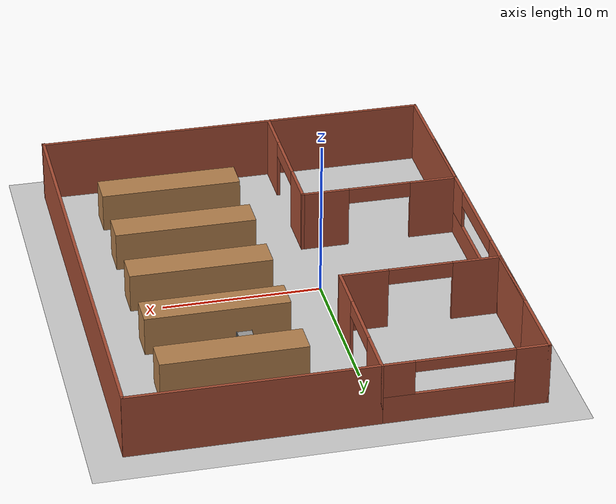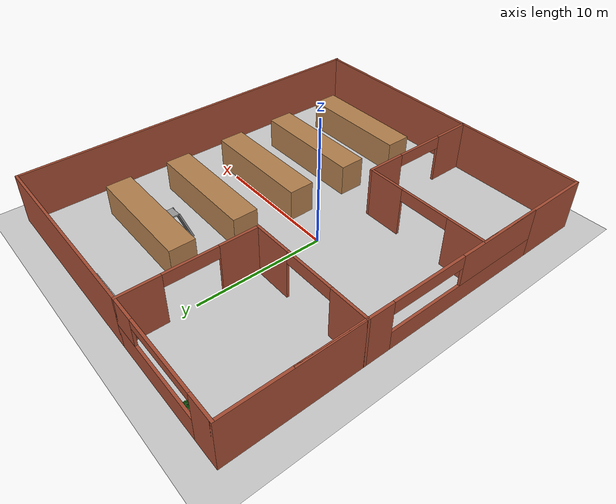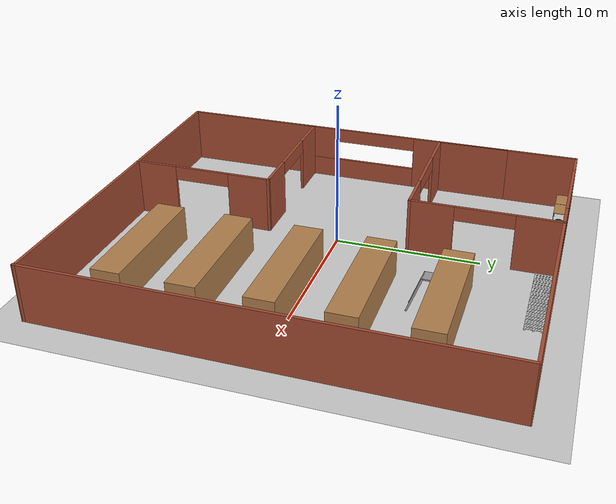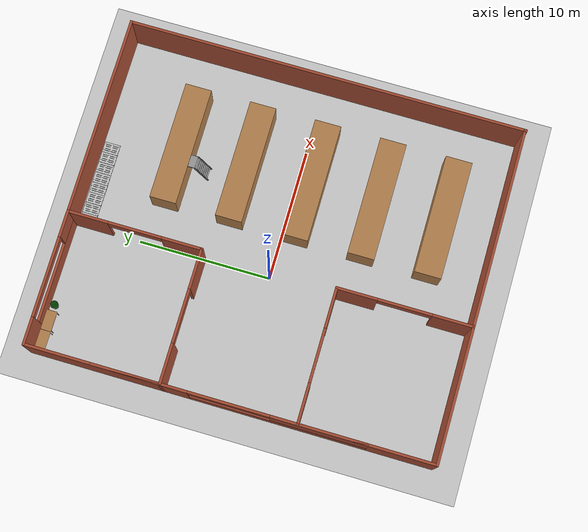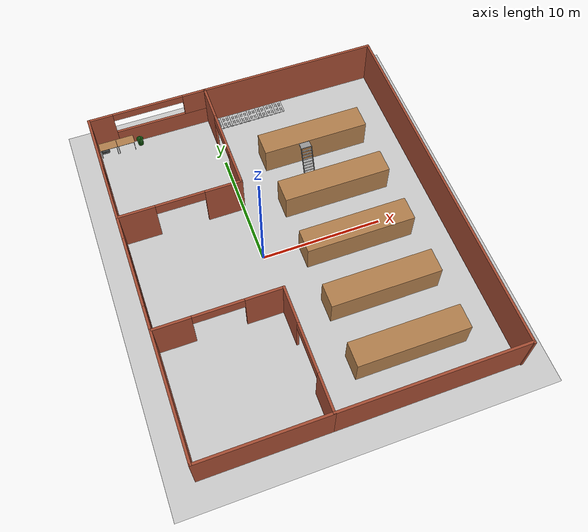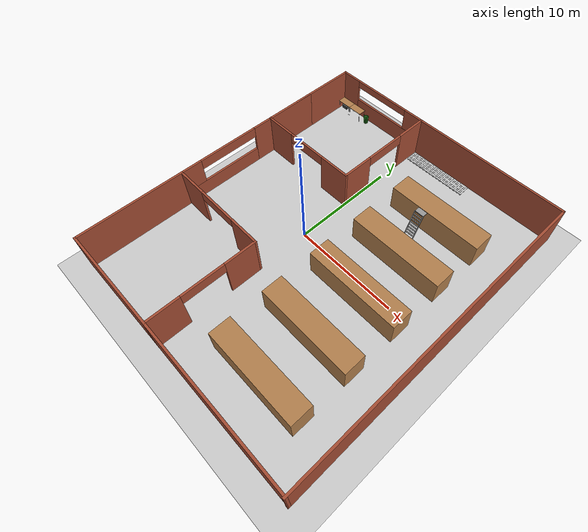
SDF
<?xml version="1.0"?>

<sdf version="1.4">
    <!--_________________ We useing a custom world to ensure ________________-->
    <!--_______________ the camera angle is launched correctly ______________-->
    <world name="default">
        <!--_________________________ ground plane __________________________-->
        <include>
            <uri>model://ground_plane</uri>
        </include>

        <!--______________________ global light source ______________________-->
        <include>
            <uri>model://sun</uri>
        </include>

        <!--________________________ WareHouse Model ________________________-->
        <model name='WareHouse'>
            <pose frame=''>2.5 -0.033501 0 0 -0 0</pose>

            <link name='Wall_12'>
                <pose frame=''>-7.5 -4.9665 0 0 -0 3.14159</pose>

                <visual name='Wall_12_Visual_0'>
                    <pose frame=''>-3.55 0 2 0 -0 0</pose>
                    <geometry>
                        <box>
                            <size>3.1 0.2 4</size>
                        </box>
                    </geometry>

                    <material>
                        <script>
                            <uri>file://media/materials/scripts/gazebo.material</uri>
                            <name>Gazebo/Bricks</name>
                        </script>
                        <ambient>1 1 1 1</ambient>
                    </material>

                    <meta>
                        <layer>0</layer>
                    </meta>
                </visual>

                <collision name='Wall_12_Collision_0'>
                    <geometry>
                        <box>
                            <size>3.1 0.2 4</size>
                        </box>
                    </geometry>
                    <pose frame=''>-3.55 0 2 0 -0 0</pose>
                </collision>

                <visual name='Wall_12_Visual_1'>
                    <pose frame=''>3.55 0 2 0 -0 0</pose>

                    <geometry>
                        <box>
                            <size>3.1 0.2 4</size>
                        </box>
                    </geometry>

                    <material>
                        <script>
                            <uri>file://media/materials/scripts/gazebo.material</uri>
                            <name>Gazebo/Bricks</name>
                        </script>

                        <ambient>1 1 1 1</ambient>
                    </material>

                    <meta>
                        <layer>0</layer>
                    </meta>
                </visual>

                <collision name='Wall_12_Collision_1'>
                    <geometry>
                        <box>
                            <size>3.1 0.2 4</size>
                        </box>
                    </geometry>

                    <pose frame=''>3.55 0 2 0 -0 0</pose>
                </collision>

                <visual name='Wall_12_Visual_2'>
                    <pose frame=''>0 0 3.5 0 -0 0</pose>
                    <geometry>
                        <box>
                            <size>4 0.2 1</size>
                        </box>
                    </geometry>

                    <material>
                        <script>
                            <uri>file://media/materials/scripts/gazebo.material</uri>
                            <name>Gazebo/Bricks</name>
                        </script>

                        <ambient>1 1 1 1</ambient>
                    </material>

                    <meta>
                        <layer>0</layer>
                    </meta>
                </visual>

                <collision name='Wall_12_Collision_2'>
                    <geometry>
                        <box>
                            <size>4 0.2 1</size>
                        </box>
                    </geometry>

                    <pose frame=''>0 0 3.5 0 -0 0</pose>
                </collision>
            </link>

            <link name='Wall_13'>
                <collision name='Wall_13_Collision'>
                    <geometry>
                        <box>
                            <size>10.2 0.2 4</size>
                        </box>
                    </geometry>

                    <pose frame=''>0 0 2 0 -0 0</pose>
                </collision>

                <visual name='Wall_13_Visual'>
                    <pose frame=''>0 0 2 0 -0 0</pose>

                    <geometry>
                        <box>
                            <size>10.2 0.2 4</size>
                        </box>
                    </geometry>

                    <material>
                        <script>
                            <uri>file://media/materials/scripts/gazebo.material</uri>
                            <name>Gazebo/Bricks</name>
                        </script>

                        <ambient>1 1 1 1</ambient>
                    </material>

                    <meta>
                        <layer>0</layer>
                    </meta>
                </visual>

                <pose frame=''>-12.5 -9.9665 0 0 -0 -1.5708</pose>
            </link>

            <link name='Wall_14'>
                <collision name='Wall_14_Collision'>
                    <geometry>
                        <box>
                            <size>10.2 0.2 4</size>
                        </box>
                    </geometry>

                    <pose frame=''>0 0 2 0 -0 0</pose>
                </collision>

                <visual name='Wall_14_Visual'>
                    <pose frame=''>0 0 2 0 -0 0</pose>

                    <geometry>
                        <box>
                            <size>10.2 0.2 4</size>
                        </box>
                    </geometry>

                    <material>
                        <script>
                            <uri>file://media/materials/scripts/gazebo.material</uri>
                            <name>Gazebo/Bricks</name>
                        </script>
                        <ambient>1 1 1 1</ambient>
                    </material>

                    <meta>
                        <layer>0</layer>
                    </meta>
                </visual>

                <pose frame=''>-7.5 -14.9665 0 0 -0 0</pose>
            </link>

            <link name='Wall_15'>
                <pose frame=''>-2.5 -9.9665 0 0 -0 1.5708</pose>

                <visual name='Wall_15_Visual_0'>
                    <pose frame=''>-3.55 0 2 0 -0 0</pose>

                    <geometry>
                        <box>
                            <size>3.1 0.2 4</size>
                        </box>
                    </geometry>

                    <material>
                        <script>
                            <uri>file://media/materials/scripts/gazebo.material</uri>
                            <name>Gazebo/Bricks</name>
                        </script>

                        <ambient>1 1 1 1</ambient>
                    </material>

                    <meta>
                        <layer>0</layer>
                    </meta>
                </visual>

                <collision name='Wall_15_Collision_0'>
                    <geometry>
                        <box>
                            <size>3.1 0.2 4</size>
                        </box>
                    </geometry>

                    <pose frame=''>-3.55 0 2 0 -0 0</pose>
                </collision>

                <visual name='Wall_15_Visual_1'>
                    <pose frame=''>3.55 0 2 0 -0 0</pose>

                    <geometry>
                        <box>
                            <size>3.1 0.2 4</size>
                        </box>
                    </geometry>

                    <material>
                        <script>
                            <uri>file://media/materials/scripts/gazebo.material</uri>
                            <name>Gazebo/Bricks</name>
                        </script>

                        <ambient>1 1 1 1</ambient>
                    </material>

                    <meta>
                        <layer>0</layer>
                    </meta>
                </visual>

                <collision name='Wall_15_Collision_1'>
                    <geometry>
                        <box>
                            <size>3.1 0.2 4</size>
                        </box>
                    </geometry>

                    <pose frame=''>3.55 0 2 0 -0 0</pose>
                </collision>

                <visual name='Wall_15_Visual_2'>
                    <pose frame=''>0 0 3.5 0 -0 0</pose>

                    <geometry>
                        <box>
                            <size>4 0.2 1</size>
                        </box>
                    </geometry>

                    <material>
                        <script>
                            <uri>file://media/materials/scripts/gazebo.material</uri>
                            <name>Gazebo/Bricks</name>
                        </script>

                        <ambient>1 1 1 1</ambient>
                    </material>

                    <meta>
                        <layer>0</layer>
                    </meta>
                </visual>

                <collision name='Wall_15_Collision_2'>
                    <geometry>
                        <box>
                            <size>4 0.2 1</size>
                        </box>
                    </geometry>

                    <pose frame=''>0 0 3.5 0 -0 0</pose>
                </collision>
            </link>

            <link name='Wall_17'>
                <pose frame=''>-12.5 0.033501 0 0 -0 -1.5708</pose>

                <visual name='Wall_17_Visual_0'>
                    <pose frame=''>-6.55 0 2 0 -0 0</pose>
                    <geometry>
                        <box>
                            <size>7.1 0.2 4</size>
                        </box>
                    </geometry>

                    <material>
                        <script>
                            <uri>file://media/materials/scripts/gazebo.material</uri>
                            <name>Gazebo/Bricks</name>
                        </script>

                        <ambient>1 1 1 1</ambient>
                    </material>

                    <meta>
                        <layer>0</layer>
                    </meta>
                </visual>

                <collision name='Wall_17_Collision_0'>
                    <geometry>
                        <box>
                            <size>7.1 0.2 4</size>
                        </box>
                    </geometry>

                    <pose frame=''>-6.55 0 2 0 -0 0</pose>
                </collision>

                <visual name='Wall_17_Visual_1'>
                    <pose frame=''>3.55 0 0.75 0 -0 0</pose>

                    <geometry>
                        <box>
                            <size>13.1 0.2 1.5</size>
                        </box>
                    </geometry>

                    <material>
                        <script>
                            <uri>file://media/materials/scripts/gazebo.material</uri>
                            <name>Gazebo/Bricks</name>
                        </script>

                        <ambient>1 1 1 1</ambient>
                    </material>

                    <meta>
                        <layer>0</layer>
                    </meta>
                </visual>

                <collision name='Wall_17_Collision_1'>
                    <geometry>
                        <box>
                            <size>13.1 0.2 1.5</size>
                        </box>
                    </geometry>

                    <pose frame=''>3.55 0 0.75 0 -0 0</pose>
                </collision>

                <visual name='Wall_17_Visual_2'>
                    <pose frame=''>6.55 0 2.75 0 -0 0</pose>

                    <geometry>
                        <box>
                            <size>7.1 0.2 2.5</size>
                        </box>
                    </geometry>

                    <material>
                        <script>
                            <uri>file://media/materials/scripts/gazebo.material</uri>
                            <name>Gazebo/Bricks</name>
                        </script>

                        <ambient>1 1 1 1</ambient>
                    </material>

                    <meta>
                        <layer>0</layer>
                    </meta>
                </visual>

                <collision name='Wall_17_Collision_2'>
                    <geometry>
                        <box>
                            <size>7.1 0.2 2.5</size>
                        </box>
                    </geometry>

                    <pose frame=''>6.55 0 2.75 0 -0 0</pose>
                </collision>

                <visual name='Wall_17_Visual_3'>
                    <pose frame=''>0 0 3.5 0 -0 0</pose>

                    <geometry>
                        <box>
                            <size>6 0.2 1</size>
                        </box>
                    </geometry>

                    <material>
                        <script>
                            <uri>file://media/materials/scripts/gazebo.material</uri>
                            <name>Gazebo/Bricks</name>
                        </script>

                        <ambient>1 1 1 1</ambient>
                    </material>

                    <meta>
                        <layer>0</layer>
                    </meta>
                </visual>

                <collision name='Wall_17_Collision_3'>
                    <geometry>
                        <box>
                            <size>6 0.2 1</size>
                        </box>
                    </geometry>

                    <pose frame=''>0 0 3.5 0 -0 0</pose>
                </collision>
            </link>

            <link name='Wall_19'>
                <collision name='Wall_19_Collision'>
                    <geometry>
                        <box>
                            <size>15.2 0.2 4</size>
                        </box>
                    </geometry>

                    <pose frame=''>0 0 2 0 -0 0</pose>
                </collision>

                <visual name='Wall_19_Visual'>
                    <pose frame=''>0 0 2 0 -0 0</pose>

                    <geometry>
                        <box>
                            <size>15.2 0.2 4</size>
                        </box>
                    </geometry>

                    <material>
                        <script>
                            <uri>file://media/materials/scripts/gazebo.material</uri>
                            <name>Gazebo/Bricks</name>
                        </script>

                        <ambient>1 1 1 1</ambient>
                    </material>

                    <meta>
                        <layer>0</layer>
                    </meta>
                </visual>

                <pose frame=''>5 15.0335 0 0 -0 0</pose>
            </link>

            <link name='Wall_2'>
                <pose frame=''>-7.5 15.0335 0 0 -0 0</pose>

                <visual name='Wall_2_Visual_0'>
                    <pose frame=''>-4.04112 0 2 0 -0 0</pose>
                    <geometry>
                        <box>
                            <size>2.11776 0.2 4</size>
                        </box>
                    </geometry>

                    <material>
                        <script>
                            <uri>file://media/materials/scripts/gazebo.material</uri>
                            <name>Gazebo/Bricks</name>
                        </script>

                        <ambient>1 1 1 1</ambient>
                    </material>

                    <meta>
                        <layer>0</layer>
                    </meta>
                </visual>

                <collision name='Wall_2_Collision_0'>
                    <geometry>
                        <box>
                            <size>2.11776 0.2 4</size>
                        </box>
                    </geometry>

                    <pose frame=''>-4.04112 0 2 0 -0 0</pose>
                </collision>

                <visual name='Wall_2_Visual_1'>
                    <pose frame=''>1.05888 0 0.9 0 -0 0</pose>

                    <geometry>
                        <box>
                            <size>8.08224 0.2 1.8</size>
                        </box>
                    </geometry>

                    <material>
                        <script>
                            <uri>file://media/materials/scripts/gazebo.material</uri>
                            <name>Gazebo/Bricks</name>
                        </script>

                        <ambient>1 1 1 1</ambient>
                    </material>

                    <meta>
                        <layer>0</layer>
                    </meta>
                </visual>

                <collision name='Wall_2_Collision_1'>
                    <geometry>
                        <box>
                            <size>8.08224 0.2 1.8</size>
                        </box>
                    </geometry>

                    <pose frame=''>1.05888 0 0.9 0 -0 0</pose>
                </collision>

                <visual name='Wall_2_Visual_2'>
                    <pose frame=''>4.05888 0 2.9 0 -0 0</pose>

                    <geometry>
                        <box>
                            <size>2.08224 0.2 2.2</size>
                        </box>
                    </geometry>

                    <material>
                        <script>
                            <uri>file://media/materials/scripts/gazebo.material</uri>
                            <name>Gazebo/Bricks</name>
                        </script>

                        <ambient>1 1 1 1</ambient>
                    </material>

                    <meta>
                        <layer>0</layer>
                    </meta>
                </visual>

                <collision name='Wall_2_Collision_2'>
                    <geometry>
                        <box>
                            <size>2.08224 0.2 2.2</size>
                        </box>
                    </geometry>

                    <pose frame=''>4.05888 0 2.9 0 -0 0</pose>
                </collision>

                <visual name='Wall_2_Visual_3'>
                    <pose frame=''>0.01776 0 3.65 0 -0 0</pose>

                    <geometry>
                        <box>
                            <size>6 0.2 0.7</size>
                        </box>
                    </geometry>

                    <material>
                        <script>
                            <uri>file://media/materials/scripts/gazebo.material</uri>
                            <name>Gazebo/Bricks</name>
                        </script>

                        <ambient>1 1 1 1</ambient>
                    </material>

                    <meta>
                        <layer>0</layer>
                    </meta>
                </visual>

                <collision name='Wall_2_Collision_3'>
                    <geometry>
                        <box>
                            <size>6 0.2 0.7</size>
                        </box>
                    </geometry>

                    <pose frame=''>0.01776 0 3.65 0 -0 0</pose>
                </collision>
            </link>

            <link name='Wall_21'>
                <collision name='Wall_21_Collision'>
                    <geometry>
                        <box>
                            <size>30.2 0.2 4</size>
                        </box>
                    </geometry>

                    <pose frame=''>0 0 2 0 -0 0</pose>
                </collision>

                <visual name='Wall_21_Visual'>
                    <pose frame=''>0 0 2 0 -0 0</pose>

                    <geometry>
                        <box>
                            <size>30.2 0.2 4</size>
                        </box>
                    </geometry>

                    <material>
                        <script>
                            <uri>file://media/materials/scripts/gazebo.material</uri>
                            <name>Gazebo/Bricks</name>
                        </script>

                        <ambient>1 1 1 1</ambient>
                    </material>

                    <meta>
                        <layer>0</layer>
                    </meta>
                </visual>

                <pose frame=''>12.5 -0.033499 0 0 -0 -1.5708</pose>
            </link>

            <link name='Wall_23'>
                <collision name='Wall_23_Collision'>
                    <geometry>
                        <box>
                            <size>15.2 0.2 4</size>
                        </box>
                    </geometry>

                    <pose frame=''>0 0 2 0 -0 0</pose>
                </collision>

                <visual name='Wall_23_Visual'>
                    <pose frame=''>0 0 2 0 -0 0</pose>

                    <geometry>
                        <box>
                            <size>15.2 0.2 4</size>
                        </box>
                    </geometry>

                    <material>
                        <script>
                            <uri>file://media/materials/scripts/gazebo.material</uri>
                            <name>Gazebo/Bricks</name>
                        </script>

                        <ambient>1 1 1 1</ambient>
                    </material>

                    <meta>
                        <layer>0</layer>
                    </meta>
                </visual>

                <pose frame=''>5 -14.9665 0 0 -0 0</pose>
            </link>

            <link name='Wall_4'>
                <pose frame=''>-2.5 10.0335 0 0 -0 -1.5708</pose>

                <visual name='Wall_4_Visual_0'>
                    <pose frame=''>-3.54841 0 2 0 -0 0</pose>

                    <geometry>
                        <box>
                            <size>3.10318 0.2 4</size>
                        </box>
                    </geometry>

                    <material>
                        <script>
                            <uri>file://media/materials/scripts/gazebo.material</uri>
                            <name>Gazebo/Bricks</name>
                        </script>

                        <ambient>1 1 1 1</ambient>
                    </material>

                    <meta>
                        <layer>0</layer>
                    </meta>
                </visual>

                <collision name='Wall_4_Collision_0'>
                    <geometry>
                        <box>
                            <size>3.10318 0.2 4</size>
                        </box>
                    </geometry>

                    <pose frame=''>-3.54841 0 2 0 -0 0</pose>
                </collision>

                <visual name='Wall_4_Visual_1'>
                    <pose frame=''>3.55159 0 2 0 -0 0</pose>

                    <geometry>
                        <box>
                            <size>3.09682 0.2 4</size>
                        </box>
                    </geometry>

                    <material>
                        <script>
                            <uri>file://media/materials/scripts/gazebo.material</uri>
                            <name>Gazebo/Bricks</name>
                        </script>

                        <ambient>1 1 1 1</ambient>
                    </material>

                    <meta>
                        <layer>0</layer>
                    </meta>
                </visual>

                <collision name='Wall_4_Collision_1'>
                    <geometry>
                        <box>
                            <size>3.09682 0.2 4</size>
                        </box>
                    </geometry>

                    <pose frame=''>3.55159 0 2 0 -0 0</pose>
                </collision>

                <visual name='Wall_4_Visual_2'>
                    <pose frame=''>0.003178 0 3.5 0 -0 0</pose>

                    <geometry>
                        <box>
                            <size>4 0.2 1</size>
                        </box>
                    </geometry>

                    <material>
                        <script>
                            <uri>file://media/materials/scripts/gazebo.material</uri>
                            <name>Gazebo/Bricks</name>
                        </script>

                        <ambient>1 1 1 1</ambient>
                    </material>

                    <meta>
                        <layer>0</layer>
                    </meta>
                </visual>

                <collision name='Wall_4_Collision_2'>
                    <geometry>
                        <box>
                            <size>4 0.2 1</size>
                        </box>
                    </geometry>

                    <pose frame=''>0.003178 0 3.5 0 -0 0</pose>
                </collision>
            </link>

            <link name='Wall_5'>
                <pose frame=''>-7.5 5.0335 0 0 -0 3.14159</pose>

                <visual name='Wall_5_Visual_0'>
                    <pose frame=''>-3.55 0 2 0 -0 0</pose>

                    <geometry>
                        <box>
                            <size>3.1 0.2 4</size>
                        </box>
                    </geometry>

                    <material>
                        <script>
                            <uri>file://media/materials/scripts/gazebo.material</uri>
                            <name>Gazebo/Bricks</name>
                        </script>

                        <ambient>1 1 1 1</ambient>
                    </material>

                    <meta>
                        <layer>0</layer>
                    </meta>
                </visual>

                <collision name='Wall_5_Collision_0'>
                    <geometry>
                        <box>
                            <size>3.1 0.2 4</size>
                        </box>
                    </geometry>

                    <pose frame=''>-3.55 0 2 0 -0 0</pose>
                </collision>

                <visual name='Wall_5_Visual_1'>
                    <pose frame=''>3.55 0 2 0 -0 0</pose>

                    <geometry>
                        <box>
                            <size>3.1 0.2 4</size>
                        </box>
                    </geometry>

                    <material>
                        <script>
                            <uri>file://media/materials/scripts/gazebo.material</uri>
                            <name>Gazebo/Bricks</name>
                        </script>

                        <ambient>1 1 1 1</ambient>
                    </material>

                    <meta>
                        <layer>0</layer>
                    </meta>
                </visual>

                <collision name='Wall_5_Collision_1'>
                    <geometry>
                        <box>
                            <size>3.1 0.2 4</size>
                        </box>
                    </geometry>

                    <pose frame=''>3.55 0 2 0 -0 0</pose>
                </collision>

                <visual name='Wall_5_Visual_2'>
                    <pose frame=''>0 0 3.5 0 -0 0</pose>

                    <geometry>
                        <box>
                            <size>4 0.2 1</size>
                        </box>
                    </geometry>

                    <material>
                        <script>
                            <uri>file://media/materials/scripts/gazebo.material</uri>
                            <name>Gazebo/Bricks</name>
                        </script>

                        <ambient>1 1 1 1</ambient>
                    </material>

                    <meta>
                        <layer>0</layer>
                    </meta>
                </visual>

                <collision name='Wall_5_Collision_2'>
                    <geometry>
                        <box>
                            <size>4 0.2 1</size>
                        </box>
                    </geometry>

                    <pose frame=''>0 0 3.5 0 -0 0</pose>
                </collision>
            </link>

            <link name='Wall_6'>
                <collision name='Wall_6_Collision'>
                    <geometry>
                        <box>
                            <size>10.2 0.2 4</size>
                        </box>
                    </geometry>

                    <pose frame=''>0 0 2 0 -0 0</pose>
                </collision>

                <visual name='Wall_6_Visual'>
                    <pose frame=''>0 0 2 0 -0 0</pose>

                    <geometry>
                        <box>
                            <size>10.2 0.2 4</size>
                        </box>
                    </geometry>

                    <material>
                        <script>
                            <uri>file://media/materials/scripts/gazebo.material</uri>
                            <name>Gazebo/Bricks</name>
                        </script>

                        <ambient>1 1 1 1</ambient>
                    </material>

                    <meta>
                        <layer>0</layer>
                    </meta>
                </visual>

                <pose frame=''>-12.5 10.0335 0 0 -0 1.5708</pose>
            </link>

            <!--_________________________ Utilities _________________________-->
            <link name='link_0'>
                <inertial>
                    <mass>1e+08</mass>
                    <inertia>
                        <ixx>1.66667e+07</ixx>
                        <ixy>0</ixy>
                        <ixz>0</ixz>
                        <iyy>1.66667e+07</iyy>
                        <iyz>0</iyz>
                        <izz>1.66667e+07</izz>
                    </inertia>
                    <pose frame=''>0 0 0 0 -0 0</pose>
                </inertial>

                <pose frame=''>5 9 1.25 0 -0 0</pose>

                <visual name='visual'>
                    <pose frame=''>0 0 0 0 -0 0</pose>

                    <geometry>
                        <box>
                            <size>9 2 2.5</size>
                        </box>
                    </geometry>

                    <material>
                        <lighting>1</lighting>
                        <script>
                            <uri>file://media/materials/scripts/gazebo.material</uri>
                            <name>Gazebo/Wood</name>
                        </script>

                        <shader type='pixel'>
                            <normal_map>__default__</normal_map>
                        </shader>

                        <ambient>0.3 0.3 0.3 1</ambient>
                        <diffuse>0.7 0.7 0.7 1</diffuse>
                        <specular>0.01 0.01 0.01 1</specular>
                        <emissive>0 0 0 1</emissive>
                    </material>
                    <transparency>0</transparency>
                    <cast_shadows>1</cast_shadows>
                </visual>

                <collision name='collision'>
                    <laser_retro>0</laser_retro>
                    <max_contacts>10</max_contacts>
                    <pose frame=''>0 0 0 0 -0 0</pose>

                    <geometry>
                        <box>
                            <size>9 2 2.5</size>
                        </box>
                    </geometry>

                    <surface>
                        <friction>
                            <ode>
                                <mu>1</mu>
                                <mu2>1</mu2>
                                <fdir1>0 0 0</fdir1>
                                <slip1>0</slip1>
                                <slip2>0</slip2>
                            </ode>

                            <torsional>
                                <coefficient>1</coefficient>
                                <patch_radius>0</patch_radius>
                                <surface_radius>0</surface_radius>
                                <use_patch_radius>1</use_patch_radius>
                                <ode>
                                    <slip>0</slip>
                                </ode>
                            </torsional>
                        </friction>

                        <bounce>
                            <restitution_coefficient>0</restitution_coefficient>
                            <threshold>1e+06</threshold>
                        </bounce>

                        <contact>
                            <collide_without_contact>0</collide_without_contact>
                            <collide_without_contact_bitmask>1</collide_without_contact_bitmask>
                            <collide_bitmask>1</collide_bitmask>

                            <ode>
                                <soft_cfm>0</soft_cfm>
                                <soft_erp>0.2</soft_erp>
                                <kp>1e+13</kp>
                                <kd>1</kd>
                                <max_vel>0.01</max_vel>
                                <min_depth>0</min_depth>
                            </ode>

                            <bullet>
                                <split_impulse>1</split_impulse>
                                <split_impulse_penetration_threshold>-0.01</split_impulse_penetration_threshold>
                                <soft_cfm>0</soft_cfm>
                                <soft_erp>0.2</soft_erp>
                                <kp>1e+13</kp>
                                <kd>1</kd>
                            </bullet>
                        </contact>
                    </surface>
                </collision>
            </link>

            <link name='link_0_clone'>
                <inertial>
                    <mass>1e+08</mass>

                    <inertia>
                        <ixx>1.66667e+07</ixx>
                        <ixy>0</ixy>
                        <ixz>0</ixz>
                        <iyy>1.66667e+07</iyy>
                        <iyz>0</iyz>
                        <izz>1.66667e+07</izz>
                    </inertia>

                    <pose frame=''>0 0 0 0 -0 0</pose>
                </inertial>

                <pose frame=''>5 4 1.25 0 -0 0</pose>
                <gravity>1</gravity>
                <self_collide>0</self_collide>
                <kinematic>0</kinematic>
                <enable_wind>0</enable_wind>

                <visual name='visual'>
                    <pose frame=''>0 0 0 0 -0 0</pose>
                    <geometry>
                        <box>
                            <size>9 2 2.5</size>
                        </box>
                    </geometry>

                    <material>
                        <lighting>1</lighting>

                        <script>
                            <uri>file://media/materials/scripts/gazebo.material</uri>
                            <name>Gazebo/Wood</name>
                        </script>
                        <shader type='pixel'>
                            <normal_map>__default__</normal_map>
                        </shader>

                        <ambient>0.3 0.3 0.3 1</ambient>
                        <diffuse>0.7 0.7 0.7 1</diffuse>
                        <specular>0.01 0.01 0.01 1</specular>
                        <emissive>0 0 0 1</emissive>
                    </material>

                    <transparency>0</transparency>
                    <cast_shadows>1</cast_shadows>
                </visual>

                <collision name='collision'>
                    <laser_retro>0</laser_retro>
                    <max_contacts>10</max_contacts>
                    <pose frame=''>0 0 0 0 -0 0</pose>

                    <geometry>
                        <box>
                            <size>9 2 2.5</size>
                        </box>
                    </geometry>

                    <surface>
                        <friction>
                            <ode>
                                <mu>1</mu>
                                <mu2>1</mu2>
                                <fdir1>0 0 0</fdir1>
                                <slip1>0</slip1>
                                <slip2>0</slip2>
                            </ode>

                            <torsional>
                                <coefficient>1</coefficient>
                                <patch_radius>0</patch_radius>
                                <surface_radius>0</surface_radius>
                                <use_patch_radius>1</use_patch_radius>

                                <ode>
                                    <slip>0</slip>
                                </ode>
                            </torsional>
                        </friction>

                        <bounce>
                            <restitution_coefficient>0</restitution_coefficient>
                            <threshold>1e+06</threshold>
                        </bounce>

                        <contact>
                            <collide_without_contact>0</collide_without_contact>
                            <collide_without_contact_bitmask>1</collide_without_contact_bitmask>
                            <collide_bitmask>1</collide_bitmask>

                            <ode>
                                <soft_cfm>0</soft_cfm>
                                <soft_erp>0.2</soft_erp>
                                <kp>1e+13</kp>
                                <kd>1</kd>
                                <max_vel>0.01</max_vel>
                                <min_depth>0</min_depth>
                            </ode>

                            <bullet>
                                <split_impulse>1</split_impulse>
                                <split_impulse_penetration_threshold>-0.01</split_impulse_penetration_threshold>
                                <soft_cfm>0</soft_cfm>
                                <soft_erp>0.2</soft_erp>
                                <kp>1e+13</kp>
                                <kd>1</kd>
                            </bullet>
                        </contact>
                    </surface>
                </collision>
            </link>

            <link name='link_0_clone_0'>
                <inertial>
                    <mass>1e+08</mass>

                    <inertia>
                        <ixx>1.66667e+07</ixx>
                        <ixy>0</ixy>
                        <ixz>0</ixz>
                        <iyy>1.66667e+07</iyy>
                        <iyz>0</iyz>
                        <izz>1.66667e+07</izz>
                    </inertia>

                    <pose frame=''>0 0 0 0 -0 0</pose>
                </inertial>

                <pose frame=''>5 -1 1.25 0 -0 0</pose>
                <gravity>1</gravity>
                <self_collide>0</self_collide>
                <kinematic>0</kinematic>
                <enable_wind>0</enable_wind>

                <visual name='visual'>
                    <pose frame=''>0 0 0 0 -0 0</pose>

                    <geometry>
                        <box>
                            <size>9 2 2.5</size>
                        </box>
                    </geometry>

                    <material>
                        <lighting>1</lighting>

                        <script>
                            <uri>file://media/materials/scripts/gazebo.material</uri>
                            <name>Gazebo/Wood</name>
                        </script>

                        <shader type='pixel'>
                            <normal_map>__default__</normal_map>
                        </shader>

                        <ambient>0.3 0.3 0.3 1</ambient>
                        <diffuse>0.7 0.7 0.7 1</diffuse>
                        <specular>0.01 0.01 0.01 1</specular>
                        <emissive>0 0 0 1</emissive>
                    </material>

                    <transparency>0</transparency>
                    <cast_shadows>1</cast_shadows>
                </visual>

                <collision name='collision'>
                    <laser_retro>0</laser_retro>
                    <max_contacts>10</max_contacts>
                    <pose frame=''>0 0 0 0 -0 0</pose>

                    <geometry>
                        <box>
                            <size>9 2 2.5</size>
                        </box>
                    </geometry>

                    <surface>
                        <friction>
                            <ode>
                                <mu>1</mu>
                                <mu2>1</mu2>
                                <fdir1>0 0 0</fdir1>
                                <slip1>0</slip1>
                                <slip2>0</slip2>
                            </ode>

                            <torsional>
                                <coefficient>1</coefficient>
                                <patch_radius>0</patch_radius>
                                <surface_radius>0</surface_radius>
                                <use_patch_radius>1</use_patch_radius>

                                <ode>
                                    <slip>0</slip>
                                </ode>
                            </torsional>
                        </friction>

                        <bounce>
                            <restitution_coefficient>0</restitution_coefficient>
                            <threshold>1e+06</threshold>
                        </bounce>

                        <contact>
                            <collide_without_contact>0</collide_without_contact>
                            <collide_without_contact_bitmask>1</collide_without_contact_bitmask>
                            <collide_bitmask>1</collide_bitmask>

                            <ode>
                                <soft_cfm>0</soft_cfm>
                                <soft_erp>0.2</soft_erp>
                                <kp>1e+13</kp>
                                <kd>1</kd>
                                <max_vel>0.01</max_vel>
                                <min_depth>0</min_depth>
                            </ode>

                            <bullet>
                                <split_impulse>1</split_impulse>
                                <split_impulse_penetration_threshold>-0.01</split_impulse_penetration_threshold>
                                <soft_cfm>0</soft_cfm>
                                <soft_erp>0.2</soft_erp>
                                <kp>1e+13</kp>
                                <kd>1</kd>
                            </bullet>
                        </contact>
                    </surface>
                </collision>
            </link>

            <link name='link_0_clone_0_clone'>
                <inertial>
                    <mass>1e+08</mass>

                    <inertia>
                        <ixx>1.66667e+07</ixx>
                        <ixy>0</ixy>
                        <ixz>0</ixz>
                        <iyy>1.66667e+07</iyy>
                        <iyz>0</iyz>
                        <izz>1.66667e+07</izz>
                    </inertia>

                    <pose frame=''>0 0 0 0 -0 0</pose>
                </inertial>

                <pose frame=''>5 -6 1.25 0 -0 0</pose>
                <gravity>1</gravity>
                <self_collide>0</self_collide>
                <kinematic>0</kinematic>
                <enable_wind>0</enable_wind>

                <visual name='visual'>
                    <pose frame=''>0 0 0 0 -0 0</pose>

                    <geometry>
                        <box>
                            <size>9 2 2.5</size>
                        </box>
                    </geometry>

                    <material>
                        <lighting>1</lighting>

                        <script>
                            <uri>file://media/materials/scripts/gazebo.material</uri>
                            <name>Gazebo/Wood</name>
                        </script>

                        <shader type='pixel'>
                            <normal_map>__default__</normal_map>
                        </shader>

                        <ambient>0.3 0.3 0.3 1</ambient>
                        <diffuse>0.7 0.7 0.7 1</diffuse>
                        <specular>0.01 0.01 0.01 1</specular>
                        <emissive>0 0 0 1</emissive>
                    </material>

                    <transparency>0</transparency>
                    <cast_shadows>1</cast_shadows>
                </visual>

                <collision name='collision'>
                    <laser_retro>0</laser_retro>
                    <max_contacts>10</max_contacts>
                    <pose frame=''>0 0 0 0 -0 0</pose>

                    <geometry>
                        <box>
                            <size>9 2 2.5</size>
                        </box>
                    </geometry>

                    <surface>
                        <friction>
                            <ode>
                                <mu>1</mu>
                                <mu2>1</mu2>
                                <fdir1>0 0 0</fdir1>
                                <slip1>0</slip1>
                                <slip2>0</slip2>
                            </ode>

                            <torsional>
                                <coefficient>1</coefficient>
                                <patch_radius>0</patch_radius>
                                <surface_radius>0</surface_radius>
                                <use_patch_radius>1</use_patch_radius>
                                <ode>
                                    <slip>0</slip>
                                </ode>
                            </torsional>
                        </friction>

                        <bounce>
                            <restitution_coefficient>0</restitution_coefficient>
                            <threshold>1e+06</threshold>
                        </bounce>

                        <contact>
                            <collide_without_contact>0</collide_without_contact>
                            <collide_without_contact_bitmask>1</collide_without_contact_bitmask>
                            <collide_bitmask>1</collide_bitmask>

                            <ode>
                                <soft_cfm>0</soft_cfm>
                                <soft_erp>0.2</soft_erp>
                                <kp>1e+13</kp>
                                <kd>1</kd>
                                <max_vel>0.01</max_vel>
                                <min_depth>0</min_depth>
                            </ode>

                            <bullet>
                                <split_impulse>1</split_impulse>
                                <split_impulse_penetration_threshold>-0.01</split_impulse_penetration_threshold>
                                <soft_cfm>0</soft_cfm>
                                <soft_erp>0.2</soft_erp>
                                <kp>1e+13</kp>
                                <kd>1</kd>
                            </bullet>
                        </contact>
                    </surface>
                </collision>
            </link>

            <link name='link_0_clone_0_clone_0'>
                <inertial>
                    <mass>1e+08</mass>

                    <inertia>
                        <ixx>1.66667e+07</ixx>
                        <ixy>0</ixy>
                        <ixz>0</ixz>
                        <iyy>1.66667e+07</iyy>
                        <iyz>0</iyz>
                        <izz>1.66667e+07</izz>
                    </inertia>

                    <pose frame=''>0 0 0 0 -0 0</pose>
                </inertial>

                <pose frame=''>5 -11 1.25 0 -0 0</pose>
                <gravity>1</gravity>
                <self_collide>0</self_collide>
                <kinematic>0</kinematic>
                <enable_wind>0</enable_wind>

                <visual name='visual'>
                    <pose frame=''>0 0 0 0 -0 0</pose>

                    <geometry>
                        <box>
                            <size>9 2 2.5</size>
                        </box>
                    </geometry>

                    <material>
                        <lighting>1</lighting>

                        <script>
                            <uri>file://media/materials/scripts/gazebo.material</uri>
                            <name>Gazebo/Wood</name>
                        </script>

                        <shader type='pixel'>
                            <normal_map>__default__</normal_map>
                        </shader>

                        <ambient>0.3 0.3 0.3 1</ambient>
                        <diffuse>0.7 0.7 0.7 1</diffuse>
                        <specular>0.01 0.01 0.01 1</specular>
                        <emissive>0 0 0 1</emissive>
                    </material>

                    <transparency>0</transparency>
                    <cast_shadows>1</cast_shadows>
                </visual>

                <collision name='collision'>
                    <laser_retro>0</laser_retro>
                    <max_contacts>10</max_contacts>
                    <pose frame=''>0 0 0 0 -0 0</pose>

                    <geometry>
                        <box>
                            <size>9 2 2.5</size>
                        </box>
                    </geometry>

                    <surface>
                        <friction>
                            <ode>
                                <mu>1</mu>
                                <mu2>1</mu2>
                                <fdir1>0 0 0</fdir1>
                                <slip1>0</slip1>
                                <slip2>0</slip2>
                            </ode>

                            <torsional>
                                <coefficient>1</coefficient>
                                <patch_radius>0</patch_radius>
                                <surface_radius>0</surface_radius>
                                <use_patch_radius>1</use_patch_radius>
                                <ode>
                                    <slip>0</slip>
                                </ode>
                            </torsional>
                        </friction>

                        <bounce>
                            <restitution_coefficient>0</restitution_coefficient>
                            <threshold>1e+06</threshold>
                        </bounce>

                        <contact>
                            <collide_without_contact>0</collide_without_contact>
                            <collide_without_contact_bitmask>1</collide_without_contact_bitmask>
                            <collide_bitmask>1</collide_bitmask>
                            <ode>
                                <soft_cfm>0</soft_cfm>
                                <soft_erp>0.2</soft_erp>
                                <kp>1e+13</kp>
                                <kd>1</kd>
                                <max_vel>0.01</max_vel>
                                <min_depth>0</min_depth>
                            </ode>

                            <bullet>
                                <split_impulse>1</split_impulse>
                                <split_impulse_penetration_threshold>-0.01</split_impulse_penetration_threshold>
                                <soft_cfm>0</soft_cfm>
                                <soft_erp>0.2</soft_erp>
                                <kp>1e+13</kp>
                                <kd>1</kd>
                            </bullet>
                        </contact>
                    </surface>
                </collision>
            </link>

            <model name='euro_pallet'>
                <link name='link'>
                    <pose frame=''>0 0 0 0 -0 0</pose>

                    <inertial>
                        <mass>20</mass>
                        <inertia>
                            <ixx>2.43</ixx>
                            <ixy>0</ixy>
                            <ixz>0</ixz>
                            <iyy>1.1</iyy>
                            <iyz>0</iyz>
                            <izz>3.47</izz>
                        </inertia>
                        <pose frame=''>0 0 0 0 -0 0</pose>
                    </inertial>

                    <collision name='collision'>
                        <pose frame=''>0 0 0.05 0 -0 0</pose>

                        <geometry>
                            <mesh>
                                <uri>model://euro_pallet/meshes/pallet.dae</uri>
                                <scale>0.1 0.1 0.1</scale>
                            </mesh>
                        </geometry>

                        <max_contacts>10</max_contacts>

                        <surface>
                            <contact>
                                <ode/>
                            </contact>

                            <bounce/>

                            <friction>
                                <torsional>
                                    <ode/>
                                </torsional>

                                <ode/>
                            </friction>
                        </surface>
                    </collision>

                    <visual name='visual'>
                        <pose frame=''>0 0 0.05 0 -0 0</pose>

                        <geometry>
                            <mesh>
                                <uri>model://euro_pallet/meshes/pallet.dae</uri>
                                <scale>0.1 0.1 0.1</scale>
                            </mesh>
                        </geometry>
                    </visual>

                    <self_collide>0</self_collide>
                    <enable_wind>0</enable_wind>
                    <kinematic>0</kinematic>
                </link>

                <pose frame=''>-1.91189 14.2628 0 0 -0 0</pose>
            </model>

            <model name='euro_pallet_0'>
                <link name='link'>
                    <pose frame=''>0 0 0 0 -0 0</pose>

                    <inertial>
                        <mass>20</mass>

                        <inertia>
                            <ixx>2.43</ixx>
                            <ixy>0</ixy>
                            <ixz>0</ixz>
                            <iyy>1.1</iyy>
                            <iyz>0</iyz>
                            <izz>3.47</izz>
                        </inertia>

                        <pose frame=''>0 0 0 0 -0 0</pose>
                    </inertial>

                    <collision name='collision'>
                        <pose frame=''>0 0 0.05 0 -0 0</pose>

                        <geometry>
                            <mesh>
                                <uri>model://euro_pallet/meshes/pallet.dae</uri>
                                <scale>0.1 0.1 0.1</scale>
                            </mesh>
                        </geometry>

                        <max_contacts>10</max_contacts>

                        <surface>
                            <contact>
                                <ode/>
                            </contact>

                            <bounce/>

                            <friction>
                                <torsional>
                                    <ode/>
                                </torsional>

                                <ode/>
                            </friction>
                        </surface>
                    </collision>

                    <visual name='visual'>
                        <pose frame=''>0 0 0.05 0 -0 0</pose>

                        <geometry>
                            <mesh>
                                <uri>model://euro_pallet/meshes/pallet.dae</uri>
                                <scale>0.1 0.1 0.1</scale>
                            </mesh>
                        </geometry>
                    </visual>

                    <self_collide>0</self_collide>
                    <enable_wind>0</enable_wind>
                    <kinematic>0</kinematic>
                </link>

                <pose frame=''>-1.10471 14.2621 0 0 -0 0</pose>
            </model>

            <model name='euro_pallet_1'>
                <link name='link'>
                    <pose frame=''>0 0 0 0 -0 0</pose>

                    <inertial>
                        <mass>20</mass>

                        <inertia>
                            <ixx>2.43</ixx>
                            <ixy>0</ixy>
                            <ixz>0</ixz>
                            <iyy>1.1</iyy>
                            <iyz>0</iyz>
                            <izz>3.47</izz>
                        </inertia>

                        <pose frame=''>0 0 0 0 -0 0</pose>
                    </inertial>

                    <collision name='collision'>
                        <pose frame=''>0 0 0.05 0 -0 0</pose>

                        <geometry>
                            <mesh>
                                <uri>model://euro_pallet/meshes/pallet.dae</uri>
                                <scale>0.1 0.1 0.1</scale>
                            </mesh>
                        </geometry>

                        <max_contacts>10</max_contacts>

                        <surface>
                            <contact>
                                <ode/>
                            </contact>

                            <bounce/>

                            <friction>
                                <torsional>
                                    <ode/>
                                </torsional>

                                <ode/>
                            </friction>
                        </surface>
                    </collision>

                    <visual name='visual'>
                        <pose frame=''>0 0 0.05 0 -0 0</pose>

                        <geometry>
                            <mesh>
                                <uri>model://euro_pallet/meshes/pallet.dae</uri>
                                <scale>0.1 0.1 0.1</scale>
                            </mesh>
                        </geometry>
                    </visual>

                    <self_collide>0</self_collide>
                    <enable_wind>0</enable_wind>
                    <kinematic>0</kinematic>
                </link>

                <pose frame=''>-0.291147 14.2621 0 0 -0 0</pose>
            </model>

            <model name='euro_pallet_2'>
                <link name='link'>
                    <pose frame=''>0 0 0 0 -0 0</pose>
                    <inertial>
                        <mass>20</mass>

                        <inertia>
                            <ixx>2.43</ixx>
                            <ixy>0</ixy>
                            <ixz>0</ixz>
                            <iyy>1.1</iyy>
                            <iyz>0</iyz>
                            <izz>3.47</izz>
                        </inertia>

                        <pose frame=''>0 0 0 0 -0 0</pose>
                    </inertial>

                    <collision name='collision'>
                        <pose frame=''>0 0 0.05 0 -0 0</pose>

                        <geometry>
                            <mesh>
                                <uri>model://euro_pallet/meshes/pallet.dae</uri>
                                <scale>0.1 0.1 0.1</scale>
                            </mesh>
                        </geometry>

                        <max_contacts>10</max_contacts>

                        <surface>
                            <contact>
                                <ode/>
                            </contact>

                            <bounce/>

                            <friction>
                                <torsional>
                                    <ode/>
                                </torsional>

                                <ode/>
                            </friction>
                        </surface>
                    </collision>

                    <visual name='visual'>
                        <pose frame=''>0 0 0.05 0 -0 0</pose>

                        <geometry>
                            <mesh>
                                <uri>model://euro_pallet/meshes/pallet.dae</uri>
                                <scale>0.1 0.1 0.1</scale>
                            </mesh>
                        </geometry>
                    </visual>

                    <self_collide>0</self_collide>
                    <enable_wind>0</enable_wind>
                    <kinematic>0</kinematic>
                </link>

                <pose frame=''>0.512337 14.2599 0 0 -0 0</pose>
            </model>

            <model name='euro_pallet_3'>
                <link name='link'>
                    <pose frame=''>0 0 0 0 -0 0</pose>

                    <inertial>
                        <mass>20</mass>

                        <inertia>
                            <ixx>2.43</ixx>
                            <ixy>0</ixy>
                            <ixz>0</ixz>
                            <iyy>1.1</iyy>
                            <iyz>0</iyz>
                            <izz>3.47</izz>
                        </inertia>

                        <pose frame=''>0 0 0 0 -0 0</pose>
                    </inertial>

                    <collision name='collision'>
                        <pose frame=''>0 0 0.05 0 -0 0</pose>

                        <geometry>
                            <mesh>
                                <uri>model://euro_pallet/meshes/pallet.dae</uri>
                                <scale>0.1 0.1 0.1</scale>
                            </mesh>
                        </geometry>

                        <max_contacts>10</max_contacts>

                        <surface>
                            <contact>
                                <ode/>
                            </contact>

                            <bounce/>

                            <friction>
                                <torsional>
                                    <ode/>
                                </torsional>

                                <ode/>
                            </friction>
                        </surface>
                    </collision>

                    <visual name='visual'>
                        <pose frame=''>0 0 0.05 0 -0 0</pose>

                        <geometry>
                            <mesh>
                                <uri>model://euro_pallet/meshes/pallet.dae</uri>
                                <scale>0.1 0.1 0.1</scale>
                            </mesh>
                        </geometry>
                    </visual>

                    <self_collide>0</self_collide>
                    <enable_wind>0</enable_wind>
                    <kinematic>0</kinematic>
                </link>

                <pose frame=''>1.32208 14.2683 0 0 -0 0</pose>
            </model>

            <model name='euro_pallet_4'>
                <link name='link'>
                    <pose frame=''>0 0 0 0 -0 0</pose>

                    <inertial>
                        <mass>20</mass>

                        <inertia>
                            <ixx>2.43</ixx>
                            <ixy>0</ixy>
                            <ixz>0</ixz>
                            <iyy>1.1</iyy>
                            <iyz>0</iyz>
                            <izz>3.47</izz>
                        </inertia>

                        <pose frame=''>0 0 0 0 -0 0</pose>
                    </inertial>

                    <collision name='collision'>
                        <pose frame=''>0 0 0.05 0 -0 0</pose>

                        <geometry>
                            <mesh>
                                <uri>model://euro_pallet/meshes/pallet.dae</uri>
                                <scale>0.1 0.1 0.1</scale>
                            </mesh>
                        </geometry>

                        <max_contacts>10</max_contacts>

                        <surface>
                            <contact>
                                <ode/>
                            </contact>

                            <bounce/>

                            <friction>
                                <torsional>
                                    <ode/>
                                </torsional>

                                <ode/>
                            </friction>
                        </surface>
                    </collision>

                    <visual name='visual'>
                        <pose frame=''>0 0 0.05 0 -0 0</pose>

                        <geometry>
                            <mesh>
                                <uri>model://euro_pallet/meshes/pallet.dae</uri>
                                <scale>0.1 0.1 0.1</scale>
                            </mesh>
                        </geometry>
                    </visual>

                    <self_collide>0</self_collide>
                    <enable_wind>0</enable_wind>
                    <kinematic>0</kinematic>
                </link>

                <pose frame=''>2.13714 14.2747 0 0 -0 0</pose>
            </model>

            <model name='euro_pallet_5'>
                <link name='link'>
                    <pose frame=''>0 0 0 0 -0 0</pose>

                    <inertial>
                        <mass>20</mass>

                        <inertia>
                            <ixx>2.43</ixx>
                            <ixy>0</ixy>
                            <ixz>0</ixz>
                            <iyy>1.1</iyy>
                            <iyz>0</iyz>
                            <izz>3.47</izz>
                        </inertia>

                        <pose frame=''>0 0 0 0 -0 0</pose>
                    </inertial>

                    <collision name='collision'>
                        <pose frame=''>0 0 0.05 0 -0 0</pose>

                        <geometry>
                            <mesh>
                                <uri>model://euro_pallet/meshes/pallet.dae</uri>
                                <scale>0.1 0.1 0.1</scale>
                            </mesh>
                        </geometry>

                        <max_contacts>10</max_contacts>

                        <surface>
                            <contact>
                                <ode/>
                            </contact>

                            <bounce/>

                            <friction>
                                <torsional>
                                    <ode/>
                                </torsional>

                                <ode/>
                            </friction>
                        </surface>
                    </collision>

                    <visual name='visual'>
                        <pose frame=''>0 0 0.05 0 -0 0</pose>

                        <geometry>
                            <mesh>
                                <uri>model://euro_pallet/meshes/pallet.dae</uri>
                                <scale>0.1 0.1 0.1</scale>
                            </mesh>
                        </geometry>
                    </visual>

                    <self_collide>0</self_collide>
                    <enable_wind>0</enable_wind>
                    <kinematic>0</kinematic>
                </link>

                <pose frame=''>2.95359 14.2776 0 0 -0 0</pose>
            </model>

            <model name='euro_pallet_6'>
                <link name='link'>
                    <pose frame=''>0 0 0 0 -0 0</pose>

                    <inertial>
                        <mass>20</mass>

                        <inertia>
                            <ixx>2.43</ixx>
                            <ixy>0</ixy>
                            <ixz>0</ixz>
                            <iyy>1.1</iyy>
                            <iyz>0</iyz>
                            <izz>3.47</izz>
                        </inertia>
                        <pose frame=''>0 0 0 0 -0 0</pose>
                    </inertial>

                    <collision name='collision'>
                        <pose frame=''>0 0 0.05 0 -0 0</pose>

                        <geometry>
                            <mesh>
                                <uri>model://euro_pallet/meshes/pallet.dae</uri>
                                <scale>0.1 0.1 0.1</scale>
                            </mesh>
                        </geometry>

                        <max_contacts>10</max_contacts>

                        <surface>
                            <contact>
                                <ode/>
                            </contact>

                            <bounce/>

                            <friction>
                                <torsional>
                                    <ode/>
                                </torsional>

                                <ode/>
                            </friction>
                        </surface>
                    </collision>

                    <visual name='visual'>
                        <pose frame=''>0 0 0.05 0 -0 0</pose>

                        <geometry>
                            <mesh>
                                <uri>model://euro_pallet/meshes/pallet.dae</uri>
                                <scale>0.1 0.1 0.1</scale>
                            </mesh>
                        </geometry>
                    </visual>

                    <self_collide>0</self_collide>
                    <enable_wind>0</enable_wind>
                    <kinematic>0</kinematic>
                </link>

                <pose frame=''>3.76216 14.2837 0 0 -0 0</pose>
            </model>

            <model name='first_2015_trash_can'>
                <link name='link'>
                    <inertial>
                        <pose frame=''>0 0 0.3683 0 -0 0</pose>

                        <mass>4.83076</mass>

                        <inertia>
                            <ixx>0.281534</ixx>
                            <ixy>0</ixy>
                            <ixz>0</ixz>
                            <iyy>0.281534</iyy>
                            <iyz>0</iyz>
                            <izz>0.126223</izz>
                        </inertia>
                    </inertial>

                    <visual name='visual'>
                        <geometry>
                            <mesh>
                                <uri>model://first_2015_trash_can/meshes/trash_can.dae</uri>
                            </mesh>
                        </geometry>
                    </visual>

                    <collision name='collision'>
                        <geometry>
                            <mesh>
                                <uri>model://first_2015_trash_can/meshes/trash_can.dae</uri>
                            </mesh>
                        </geometry>

                        <max_contacts>10</max_contacts>

                        <surface>
                            <contact>
                                <ode/>
                            </contact>

                            <bounce/>

                            <friction>
                                <torsional>
                                    <ode/>
                                </torsional>

                                <ode/>
                            </friction>
                        </surface>
                    </collision>

                    <self_collide>0</self_collide>
                    <enable_wind>0</enable_wind>
                    <kinematic>0</kinematic>
                </link>

                <pose frame=''>-8.83203 14.5313 0 0 -0 0</pose>
            </model>

            <model name='grey_tote'>
                <link name='link'>
                    <inertial>
                        <pose frame=''>0 0 0.14155 0 -0 0</pose>
                        <mass>3.53802</mass>

                        <inertia>
                            <ixx>0.0688358</ixx>
                            <ixy>0</ixy>
                            <ixz>0</ixz>
                            <iyy>0.139596</iyy>
                            <iyz>0</iyz>
                            <izz>0.155909</izz>
                        </inertia>
                    </inertial>

                    <collision name='lid'>
                        <pose frame=''>0 0 0.28958 0 -0 0</pose>

                        <geometry>
                            <box>
                                <size>0.67768 0.41298 0.01588</size>
                            </box>
                        </geometry>

                        <max_contacts>10</max_contacts>

                        <surface>
                            <contact>
                                <ode/>
                            </contact>

                            <bounce/>

                            <friction>
                                <torsional>
                                    <ode/>
                                </torsional>

                                <ode/>
                            </friction>
                        </surface>
                    </collision>

                    <collision name='lid_lip_1'>
                        <pose frame=''>0 0.20063 0.3048 0 -0 0</pose>

                        <geometry>
                            <box>
                                <size>0.65068 0.0105 0.0127</size>
                            </box>
                        </geometry>

                        <max_contacts>10</max_contacts>

                        <surface>
                            <contact>
                                <ode/>
                            </contact>

                            <bounce/>

                            <friction>
                                <torsional>
                                    <ode/>
                                </torsional>

                                <ode/>
                            </friction>
                        </surface>
                    </collision>

                    <collision name='lid_lip_2'>
                        <pose frame=''>0 -0.20063 0.3048 0 -0 0</pose>

                        <geometry>
                            <box>
                                <size>0.65068 0.0105 0.0127</size>
                            </box>
                        </geometry>

                        <max_contacts>10</max_contacts>

                        <surface>
                            <contact>
                                <ode/>
                            </contact>

                            <bounce/>

                            <friction>
                                <torsional>
                                    <ode/>
                                </torsional>

                                <ode/>
                            </friction>
                        </surface>
                    </collision>

                    <collision name='lid_lip_3'>
                        <pose frame=''>0.32585 0 0.3048 0 -0 0</pose>

                        <geometry>
                            <box>
                                <size>0.02602 0.31202 0.0127</size>
                            </box>
                        </geometry>

                        <max_contacts>10</max_contacts>

                        <surface>
                            <contact>
                                <ode/>
                            </contact>

                            <bounce/>

                            <friction>
                                <torsional>
                                    <ode/>
                                </torsional>

                                <ode/>
                            </friction>
                        </surface>
                    </collision>

                    <collision name='lid_lip_4'>
                        <pose frame=''>-0.32585 0 0.3048 0 -0 0</pose>

                        <geometry>
                            <box>
                                <size>0.02602 0.31202 0.0127</size>
                            </box>
                        </geometry>

                        <max_contacts>10</max_contacts>

                        <surface>
                            <contact>
                                <ode/>
                            </contact>

                            <bounce/>

                            <friction>
                                <torsional>
                                    <ode/>
                                </torsional>

                                <ode/>
                            </friction>
                        </surface>
                    </collision>

                    <collision name='side_wall_1'>
                        <pose frame=''>0 -0.18 0.14155 0.061147 -0 0</pose>

                        <geometry>
                            <box>
                                <size>0.58404 0.02602 0.283099</size>
                            </box>
                        </geometry>

                        <max_contacts>10</max_contacts>

                        <surface>
                            <contact>
                                <ode/>
                            </contact>

                            <bounce/>

                            <friction>
                                <torsional>
                                    <ode/>
                                </torsional>

                                <ode/>
                            </friction>
                        </surface>
                    </collision>

                    <collision name='side_wall_2'>
                        <pose frame=''>0 0.18 0.14155 -0.061147 0 0</pose>

                        <geometry>
                            <box>
                                <size>0.58404 0.02602 0.283099</size>
                            </box>
                        </geometry>

                        <max_contacts>10</max_contacts>

                        <surface>
                            <contact>
                                <ode/>
                            </contact>

                            <bounce/>
                            <friction>
                                <torsional>
                                    <ode/>
                                </torsional>

                                <ode/>
                            </friction>
                        </surface>
                    </collision>

                    <collision name='side_wall_3'>
                        <pose frame=''>0.305 0 0.14155 0 0.061147 0</pose>

                        <geometry>
                            <box>
                                <size>0.02602 0.33046 0.283099</size>
                            </box>
                        </geometry>

                        <max_contacts>10</max_contacts>

                        <surface>
                            <contact>
                                <ode/>
                            </contact>

                            <bounce/>

                            <friction>
                                <torsional>
                                    <ode/>
                                </torsional>

                                <ode/>
                            </friction>
                        </surface>
                    </collision>

                    <collision name='side_wall_4'>
                        <pose frame=''>-0.305 0 0.14155 0 -0.061147 0</pose>

                        <geometry>
                            <box>
                                <size>0.02602 0.33046 0.283099</size>
                            </box>
                        </geometry>

                        <max_contacts>10</max_contacts>

                        <surface>
                            <contact>
                                <ode/>
                            </contact>

                            <bounce/>

                            <friction>
                                <torsional>
                                    <ode/>
                                </torsional>

                                <ode/>
                            </friction>
                        </surface>
                    </collision>

                    <collision name='bottom'>
                        <pose frame=''>0 0 0.01 0 -0 0</pose>

                        <geometry>
                            <box>
                                <size>0.58404 0.33046 0.02</size>
                            </box>
                        </geometry>

                        <max_contacts>10</max_contacts>

                        <surface>
                            <contact>
                                <ode/>
                            </contact>

                            <bounce/>

                            <friction>
                                <torsional>
                                    <ode/>
                                </torsional>

                                <ode/>
                            </friction>
                        </surface>
                    </collision>

                    <collision name='corner_1'>
                        <pose frame=''>0.30202 -0.175 0.14155 0.061147 0.061147 -0</pose>

                        <geometry>
                            <cylinder>
                                <radius>0.01268</radius>
                                <length>0.283099</length>
                            </cylinder>
                        </geometry>

                        <max_contacts>10</max_contacts>

                        <surface>
                            <contact>
                                <ode/>
                            </contact>

                            <bounce/>

                            <friction>
                                <torsional>
                                    <ode/>
                                </torsional>

                                <ode/>
                            </friction>
                        </surface>
                    </collision>

                    <collision name='corner_2'>
                        <pose frame=''>-0.30202 -0.175 0.14155 0.061147 -0.061147 0</pose>

                        <geometry>
                            <cylinder>
                                <radius>0.01268</radius>
                                <length>0.283099</length>
                            </cylinder>
                        </geometry>

                        <max_contacts>10</max_contacts>

                        <surface>
                            <contact>
                                <ode/>
                            </contact>

                            <bounce/>

                            <friction>
                                <torsional>
                                    <ode/>
                                </torsional>

                                <ode/>
                            </friction>
                        </surface>
                    </collision>

                    <collision name='corner_3'>
                        <pose frame=''>-0.30202 0.175 0.14155 -0.061147 -0.061147 -0</pose>

                        <geometry>
                            <cylinder>
                                <radius>0.01268</radius>
                                <length>0.283099</length>
                            </cylinder>
                        </geometry>

                        <max_contacts>10</max_contacts>

                        <surface>
                            <contact>
                                <ode/>
                            </contact>

                            <bounce/>

                            <friction>
                                <torsional>
                                    <ode/>
                                </torsional>

                                <ode/>
                            </friction>
                        </surface>
                    </collision>

                    <collision name='corner_4'>
                        <pose frame=''>0.30202 0.175 0.14155 -0.061147 0.061147 0</pose>

                        <geometry>
                            <cylinder>
                                <radius>0.01268</radius>
                                <length>0.283099</length>
                            </cylinder>
                        </geometry>

                        <max_contacts>10</max_contacts>

                        <surface>
                            <contact>
                                <ode/>
                            </contact>

                            <bounce/>

                            <friction>
                                <torsional>
                                    <ode/>
                                </torsional>

                                <ode/>
                            </friction>
                        </surface>
                    </collision>

                    <visual name='visual'>
                        <geometry>
                            <mesh>
                                <uri>model://grey_tote/meshes/tote.dae</uri>
                            </mesh>
                        </geometry>
                    </visual>

                    <self_collide>0</self_collide>
                    <enable_wind>0</enable_wind>
                    <kinematic>0</kinematic>
                </link>

                <pose frame=''>-11.9152 14.6623 0 0 -0 0</pose>
            </model>

            <model name='table'>
                <static>1</static>

                <link name='link'>
                    <collision name='surface'>
                        <pose frame=''>0 0 1 0 -0 0</pose>

                        <geometry>
                            <box>
                                <size>1.5 0.8 0.03</size>
                            </box>
                        </geometry>

                        <surface>
                            <friction>
                                <ode>
                                    <mu>0.6</mu>
                                    <mu2>0.6</mu2>
                                </ode>

                                <torsional>
                                    <ode/>
                                </torsional>
                            </friction>

                            <contact>
                                <ode/>
                            </contact>

                            <bounce/>
                        </surface>

                        <max_contacts>10</max_contacts>
                    </collision>

                    <visual name='visual1'>
                        <pose frame=''>0 0 1 0 -0 0</pose>

                        <geometry>
                            <box>
                                <size>1.5 0.8 0.03</size>
                            </box>
                        </geometry>

                        <material>
                            <script>
                                <uri>file://media/materials/scripts/gazebo.material</uri>
                                <name>Gazebo/Wood</name>
                            </script>
                        </material>
                    </visual>

                    <collision name='front_left_leg'>
                        <pose frame=''>0.68 0.38 0.5 0 -0 0</pose>

                        <geometry>
                            <cylinder>
                                <radius>0.02</radius>
                                <length>1</length>
                            </cylinder>
                        </geometry>

                        <max_contacts>10</max_contacts>

                        <surface>
                            <contact>
                                <ode/>
                            </contact>

                            <bounce/>

                            <friction>
                                <torsional>
                                    <ode/>
                                </torsional>

                                <ode/>
                            </friction>
                        </surface>
                    </collision>

                    <visual name='front_left_leg'>
                        <pose frame=''>0.68 0.38 0.5 0 -0 0</pose>

                        <geometry>
                            <cylinder>
                                <radius>0.02</radius>
                                <length>1</length>
                            </cylinder>
                        </geometry>

                        <material>
                            <script>
                                <uri>file://media/materials/scripts/gazebo.material</uri>
                                <name>Gazebo/Grey</name>
                            </script>
                        </material>
                    </visual>

                    <collision name='front_right_leg'>
                        <pose frame=''>0.68 -0.38 0.5 0 -0 0</pose>

                        <geometry>
                            <cylinder>
                                <radius>0.02</radius>
                                <length>1</length>
                            </cylinder>
                        </geometry>

                        <max_contacts>10</max_contacts>

                        <surface>
                            <contact>
                                <ode/>
                            </contact>

                            <bounce/>

                            <friction>
                                <torsional>
                                    <ode/>
                                </torsional>

                                <ode/>
                            </friction>
                        </surface>
                    </collision>

                    <visual name='front_right_leg'>
                        <pose frame=''>0.68 -0.38 0.5 0 -0 0</pose>

                        <geometry>
                            <cylinder>
                                <radius>0.02</radius>
                                <length>1</length>
                            </cylinder>
                        </geometry>

                        <material>
                            <script>
                                <uri>file://media/materials/scripts/gazebo.material</uri>
                                <name>Gazebo/Grey</name>
                            </script>
                        </material>
                    </visual>

                    <collision name='back_right_leg'>
                        <pose frame=''>-0.68 -0.38 0.5 0 -0 0</pose>

                        <geometry>
                            <cylinder>
                                <radius>0.02</radius>
                                <length>1</length>
                            </cylinder>
                        </geometry>

                        <max_contacts>10</max_contacts>

                        <surface>
                            <contact>
                                <ode/>
                            </contact>

                            <bounce/>

                            <friction>
                                <torsional>
                                    <ode/>
                                </torsional>

                                <ode/>
                            </friction>
                        </surface>
                    </collision>

                    <visual name='back_right_leg'>
                        <pose frame=''>-0.68 -0.38 0.5 0 -0 0</pose>

                        <geometry>
                            <cylinder>
                                <radius>0.02</radius>
                                <length>1</length>
                            </cylinder>
                        </geometry>

                        <material>
                            <script>
                                <uri>file://media/materials/scripts/gazebo.material</uri>
                                <name>Gazebo/Grey</name>
                            </script>
                        </material>
                    </visual>

                    <collision name='back_left_leg'>
                        <pose frame=''>-0.68 0.38 0.5 0 -0 0</pose>

                        <geometry>
                            <cylinder>
                                <radius>0.02</radius>
                                <length>1</length>
                            </cylinder>
                        </geometry>

                        <max_contacts>10</max_contacts>

                        <surface>
                            <contact>
                                <ode/>
                            </contact>

                            <bounce/>

                            <friction>
                                <torsional>
                                    <ode/>
                                </torsional>

                                <ode/>
                            </friction>
                        </surface>
                    </collision>

                    <visual name='back_left_leg'>
                        <pose frame=''>-0.68 0.38 0.5 0 -0 0</pose>

                        <geometry>
                            <cylinder>
                                <radius>0.02</radius>
                                <length>1</length>
                            </cylinder>
                        </geometry>

                        <material>
                            <script>
                                <uri>file://media/materials/scripts/gazebo.material</uri>
                                <name>Gazebo/Grey</name>
                            </script>
                        </material>
                    </visual>

                    <self_collide>0</self_collide>
                    <enable_wind>0</enable_wind>
                    <kinematic>0</kinematic>
                </link>

                <pose frame=''>-11.6099 14.4729 0 0 -0 0</pose>
            </model>

            <model name='table_clone'>
                <static>1</static>
                <link name='link'>
                    <collision name='surface'>
                        <pose frame=''>0 0 1 0 -0 0</pose>

                        <geometry>
                            <box>
                                <size>1.5 0.8 0.03</size>
                            </box>
                        </geometry>

                        <surface>
                            <friction>
                                <ode>
                                    <mu>0.6</mu>
                                    <mu2>0.6</mu2>
                                </ode>

                                <torsional>
                                    <ode/>
                                </torsional>
                            </friction>

                            <contact>
                                <ode/>
                            </contact>

                            <bounce/>
                        </surface>

                        <max_contacts>10</max_contacts>
                    </collision>

                    <visual name='visual1'>
                        <pose frame=''>0 0 1 0 -0 0</pose>

                        <geometry>
                            <box>
                                <size>1.5 0.8 0.03</size>
                            </box>
                        </geometry>

                        <material>
                            <script>
                                <uri>file://media/materials/scripts/gazebo.material</uri>
                                <name>Gazebo/Wood</name>
                            </script>
                        </material>
                    </visual>

                    <collision name='front_left_leg'>
                        <pose frame=''>0.68 0.38 0.5 0 -0 0</pose>

                        <geometry>
                            <cylinder>
                                <radius>0.02</radius>
                                <length>1</length>
                            </cylinder>
                        </geometry>

                        <max_contacts>10</max_contacts>

                        <surface>
                            <contact>
                                <ode/>
                            </contact>

                            <bounce/>

                            <friction>
                                <torsional>
                                    <ode/>
                                </torsional>

                                <ode/>
                            </friction>
                        </surface>
                    </collision>

                    <visual name='front_left_leg'>
                        <pose frame=''>0.68 0.38 0.5 0 -0 0</pose>

                        <geometry>
                            <cylinder>
                                <radius>0.02</radius>
                                <length>1</length>
                            </cylinder>
                        </geometry>

                        <material>
                            <script>
                                <uri>file://media/materials/scripts/gazebo.material</uri>
                                <name>Gazebo/Grey</name>
                            </script>
                        </material>
                    </visual>

                    <collision name='front_right_leg'>
                        <pose frame=''>0.68 -0.38 0.5 0 -0 0</pose>

                        <geometry>
                            <cylinder>
                                <radius>0.02</radius>
                                <length>1</length>
                            </cylinder>
                        </geometry>

                        <max_contacts>10</max_contacts>

                        <surface>
                            <contact>
                                <ode/>
                            </contact>

                            <bounce/>

                            <friction>
                                <torsional>
                                    <ode/>
                                </torsional>

                                <ode/>
                            </friction>
                        </surface>
                    </collision>

                    <visual name='front_right_leg'>
                        <pose frame=''>0.68 -0.38 0.5 0 -0 0</pose>

                        <geometry>
                            <cylinder>
                                <radius>0.02</radius>
                                <length>1</length>
                            </cylinder>
                        </geometry>

                        <material>
                            <script>
                                <uri>file://media/materials/scripts/gazebo.material</uri>
                                <name>Gazebo/Grey</name>
                            </script>
                        </material>
                    </visual>

                    <collision name='back_right_leg'>
                        <pose frame=''>-0.68 -0.38 0.5 0 -0 0</pose>

                        <geometry>
                            <cylinder>
                                <radius>0.02</radius>
                                <length>1</length>
                            </cylinder>
                        </geometry>

                        <max_contacts>10</max_contacts>

                        <surface>
                            <contact>
                                <ode/>
                            </contact>

                            <bounce/>

                            <friction>
                                <torsional>
                                    <ode/>
                                </torsional>

                                <ode/>
                            </friction>
                        </surface>
                    </collision>

                    <visual name='back_right_leg'>
                        <pose frame=''>-0.68 -0.38 0.5 0 -0 0</pose>

                        <geometry>
                            <cylinder>
                                <radius>0.02</radius>
                                <length>1</length>
                            </cylinder>
                        </geometry>

                        <material>
                            <script>
                                <uri>file://media/materials/scripts/gazebo.material</uri>
                                <name>Gazebo/Grey</name>
                            </script>
                        </material>
                    </visual>

                    <collision name='back_left_leg'>
                        <pose frame=''>-0.68 0.38 0.5 0 -0 0</pose>

                        <geometry>
                            <cylinder>
                                <radius>0.02</radius>
                                <length>1</length>
                            </cylinder>
                        </geometry>

                        <max_contacts>10</max_contacts>

                        <surface>
                            <contact>
                                <ode/>
                            </contact>

                            <bounce/>

                            <friction>
                                <torsional>
                                    <ode/>
                                </torsional>

                                <ode/>
                            </friction>
                        </surface>
                    </collision>

                    <visual name='back_left_leg'>
                        <pose frame=''>-0.68 0.38 0.5 0 -0 0</pose>

                        <geometry>
                            <cylinder>
                                <radius>0.02</radius>
                                <length>1</length>
                            </cylinder>
                        </geometry>

                        <material>
                            <script>
                                <uri>file://media/materials/scripts/gazebo.material</uri>
                                <name>Gazebo/Grey</name>
                            </script>
                        </material>
                    </visual>

                    <self_collide>0</self_collide>
                    <enable_wind>0</enable_wind>
                    <kinematic>0</kinematic>
                </link>

                <pose frame=''>-10.0977 14.4682 0 0 -0 0</pose>
            </model>

            <model name='ladder_70deg_0rails'>
                <static>1</static>

                <link name='step0'>
                    <pose frame=''>0 0.097059 0.266667 0 -0 0</pose>

                    <inertial>
                        <mass>9.75482</mass>

                        <inertia>
                            <ixx>0.00957124</ixx>
                            <iyy>0.65963</iyy>
                            <izz>0.666842</izz>
                            <ixy>0</ixy>
                            <ixz>0</ixz>
                            <iyz>0</iyz>
                        </inertia>
                    </inertial>

                    <collision name='collision'>
                        <geometry>
                            <box>
                                <size>0.9 0.1016 0.0381</size>
                            </box>
                        </geometry>

                        <max_contacts>10</max_contacts>

                        <surface>
                            <contact>
                                <ode/>
                            </contact>

                            <bounce/>

                            <friction>
                                <torsional>
                                    <ode/>
                                </torsional>

                                <ode/>
                            </friction>
                        </surface>
                    </collision>

                    <visual name='visual'>
                        <geometry>
                            <box>
                                <size>0.9 0.1016 0.0381</size>
                            </box>
                        </geometry>

                        <material>
                            <script>
                                <uri>file://media/materials/scripts/gazebo.material</uri>
                                <name>Gazebo/Grey</name>
                            </script>
                        </material>
                    </visual>

                    <self_collide>0</self_collide>
                    <enable_wind>0</enable_wind>
                    <kinematic>0</kinematic>
                </link>

                <link name='step1'>
                    <pose frame=''>0 0.194117 0.533333 0 -0 0</pose>

                    <inertial>
                        <mass>9.75482</mass>

                        <inertia>
                            <ixx>0.00957124</ixx>
                            <iyy>0.65963</iyy>
                            <izz>0.666842</izz>
                            <ixy>0</ixy>
                            <ixz>0</ixz>
                            <iyz>0</iyz>
                        </inertia>
                    </inertial>

                    <collision name='collision'>
                        <geometry>
                            <box>
                                <size>0.9 0.1016 0.0381</size>
                            </box>
                        </geometry>

                        <max_contacts>10</max_contacts>

                        <surface>
                            <contact>
                                <ode/>
                            </contact>

                            <bounce/>

                            <friction>
                                <torsional>
                                    <ode/>
                                </torsional>

                                <ode/>
                            </friction>
                        </surface>
                    </collision>

                    <visual name='visual'>
                        <geometry>
                            <box>
                                <size>0.9 0.1016 0.0381</size>
                            </box>
                        </geometry>

                        <material>
                            <script>
                                <uri>file://media/materials/scripts/gazebo.material</uri>
                                <name>Gazebo/Grey</name>
                            </script>
                        </material>
                    </visual>

                    <self_collide>0</self_collide>
                    <enable_wind>0</enable_wind>
                    <kinematic>0</kinematic>
                </link>

                <link name='step2'>
                    <pose frame=''>0 0.291176 0.8 0 -0 0</pose>

                    <inertial>
                        <mass>9.75482</mass>

                        <inertia>
                            <ixx>0.00957124</ixx>
                            <iyy>0.65963</iyy>
                            <izz>0.666842</izz>
                            <ixy>0</ixy>
                            <ixz>0</ixz>
                            <iyz>0</iyz>
                        </inertia>
                    </inertial>

                    <collision name='collision'>
                        <geometry>
                            <box>
                                <size>0.9 0.1016 0.0381</size>
                            </box>
                        </geometry>

                        <max_contacts>10</max_contacts>

                        <surface>
                            <contact>
                                <ode/>
                            </contact>

                            <bounce/>

                            <friction>
                                <torsional>
                                    <ode/>
                                </torsional>

                                <ode/>
                            </friction>
                        </surface>
                    </collision>

                    <visual name='visual'>
                        <geometry>
                            <box>
                                <size>0.9 0.1016 0.0381</size>
                            </box>
                        </geometry>

                        <material>
                            <script>
                                <uri>file://media/materials/scripts/gazebo.material</uri>
                                <name>Gazebo/Grey</name>
                            </script>
                        </material>
                    </visual>

                    <self_collide>0</self_collide>
                    <enable_wind>0</enable_wind>
                    <kinematic>0</kinematic>
                </link>

                <link name='step3'>
                    <pose frame=''>0 0.388235 1.06667 0 -0 0</pose>

                    <inertial>
                        <mass>9.75482</mass>

                        <inertia>
                            <ixx>0.00957124</ixx>
                            <iyy>0.65963</iyy>
                            <izz>0.666842</izz>
                            <ixy>0</ixy>
                            <ixz>0</ixz>
                            <iyz>0</iyz>
                        </inertia>
                    </inertial>

                    <collision name='collision'>
                        <geometry>
                            <box>
                                <size>0.9 0.1016 0.0381</size>
                            </box>
                        </geometry>

                        <max_contacts>10</max_contacts>

                        <surface>
                            <contact>
                                <ode/>
                            </contact>

                            <bounce/>

                            <friction>
                                <torsional>
                                    <ode/>
                                </torsional>

                                <ode/>
                            </friction>
                        </surface>
                    </collision>

                    <visual name='visual'>
                        <geometry>
                            <box>
                                <size>0.9 0.1016 0.0381</size>
                            </box>
                        </geometry>

                        <material>
                            <script>
                                <uri>file://media/materials/scripts/gazebo.material</uri>
                                <name>Gazebo/Grey</name>
                            </script>
                        </material>
                    </visual>

                    <self_collide>0</self_collide>
                    <enable_wind>0</enable_wind>
                    <kinematic>0</kinematic>
                </link>

                <link name='step4'>
                    <pose frame=''>0 0.485294 1.33333 0 -0 0</pose>

                    <inertial>
                        <mass>9.75482</mass>

                        <inertia>
                            <ixx>0.00957124</ixx>
                            <iyy>0.65963</iyy>
                            <izz>0.666842</izz>
                            <ixy>0</ixy>
                            <ixz>0</ixz>
                            <iyz>0</iyz>
                        </inertia>
                    </inertial>

                    <collision name='collision'>
                        <geometry>
                            <box>
                                <size>0.9 0.1016 0.0381</size>
                            </box>
                        </geometry>

                        <max_contacts>10</max_contacts>

                        <surface>
                            <contact>
                                <ode/>
                            </contact>

                            <bounce/>

                            <friction>
                                <torsional>
                                    <ode/>
                                </torsional>

                                <ode/>
                            </friction>
                        </surface>
                    </collision>

                    <visual name='visual'>
                        <geometry>
                            <box>
                                <size>0.9 0.1016 0.0381</size>
                            </box>
                        </geometry>

                        <material>
                            <script>
                                <uri>file://media/materials/scripts/gazebo.material</uri>
                                <name>Gazebo/Grey</name>
                            </script>
                        </material>
                    </visual>

                    <self_collide>0</self_collide>
                    <enable_wind>0</enable_wind>
                    <kinematic>0</kinematic>
                </link>

                <link name='step5'>
                    <pose frame=''>0 0.582352 1.6 0 -0 0</pose>

                    <inertial>
                        <mass>9.75482</mass>

                        <inertia>
                            <ixx>0.00957124</ixx>
                            <iyy>0.65963</iyy>
                            <izz>0.666842</izz>
                            <ixy>0</ixy>
                            <ixz>0</ixz>
                            <iyz>0</iyz>
                        </inertia>
                    </inertial>

                    <collision name='collision'>
                        <geometry>
                            <box>
                                <size>0.9 0.1016 0.0381</size>
                            </box>
                        </geometry>

                        <max_contacts>10</max_contacts>

                        <surface>
                            <contact>
                                <ode/>
                            </contact>

                            <bounce/>

                            <friction>
                                <torsional>
                                    <ode/>
                                </torsional>

                                <ode/>
                            </friction>
                        </surface>
                    </collision>

                    <visual name='visual'>
                        <geometry>
                            <box>
                                <size>0.9 0.1016 0.0381</size>
                            </box>
                        </geometry>

                        <material>
                            <script>
                                <uri>file://media/materials/scripts/gazebo.material</uri>
                                <name>Gazebo/Grey</name>
                            </script>
                        </material>
                    </visual>

                    <self_collide>0</self_collide>
                    <enable_wind>0</enable_wind>
                    <kinematic>0</kinematic>
                </link>

                <link name='step6'>
                    <pose frame=''>0 0.679411 1.86667 0 -0 0</pose>

                    <inertial>
                        <mass>9.75482</mass>

                        <inertia>
                            <ixx>0.00957124</ixx>
                            <iyy>0.65963</iyy>
                            <izz>0.666842</izz>
                            <ixy>0</ixy>
                            <ixz>0</ixz>
                            <iyz>0</iyz>
                        </inertia>
                    </inertial>

                    <collision name='collision'>
                        <geometry>
                            <box>
                                <size>0.9 0.1016 0.0381</size>
                            </box>
                        </geometry>

                        <max_contacts>10</max_contacts>

                        <surface>
                            <contact>
                                <ode/>
                            </contact>

                            <bounce/>

                            <friction>
                                <torsional>
                                    <ode/>
                                </torsional>

                                <ode/>
                            </friction>
                        </surface>
                    </collision>

                    <visual name='visual'>
                        <geometry>
                            <box>
                                <size>0.9 0.1016 0.0381</size>
                            </box>
                        </geometry>

                        <material>
                            <script>
                                <uri>file://media/materials/scripts/gazebo.material</uri>
                                <name>Gazebo/Grey</name>
                            </script>
                        </material>
                    </visual>

                    <self_collide>0</self_collide>
                    <enable_wind>0</enable_wind>
                    <kinematic>0</kinematic>
                </link>

                <link name='step7'>
                    <pose frame=''>0 0.77647 2.13333 0 -0 0</pose>

                    <inertial>
                        <mass>9.75482</mass>

                        <inertia>
                            <ixx>0.00957124</ixx>
                            <iyy>0.65963</iyy>
                            <izz>0.666842</izz>
                            <ixy>0</ixy>
                            <ixz>0</ixz>
                            <iyz>0</iyz>
                        </inertia>
                    </inertial>

                    <collision name='collision'>
                        <geometry>
                            <box>
                                <size>0.9 0.1016 0.0381</size>
                            </box>
                        </geometry>

                        <max_contacts>10</max_contacts>

                        <surface>
                            <contact>
                                <ode/>
                            </contact>

                            <bounce/>

                            <friction>
                                <torsional>
                                    <ode/>
                                </torsional>

                                <ode/>
                            </friction>
                        </surface>
                    </collision>

                    <visual name='visual'>
                        <geometry>
                            <box>
                                <size>0.9 0.1016 0.0381</size>
                            </box>
                        </geometry>

                        <material>
                            <script>
                                <uri>file://media/materials/scripts/gazebo.material</uri>
                                <name>Gazebo/Grey</name>
                            </script>
                        </material>
                    </visual>

                    <self_collide>0</self_collide>
                    <enable_wind>0</enable_wind>
                    <kinematic>0</kinematic>
                </link>

                <link name='landing'>
                    <pose frame=''>0 1.17353 2.4 0 -0 0</pose>

                    <inertial>
                        <mass>57.6072</mass>

                        <inertia>
                            <ixx>1.73518</ixx>
                            <iyy>3.89545</iyy>
                            <izz>5.6167</izz>
                            <ixy>0</ixy>
                            <ixz>0</ixz>
                            <iyz>0</iyz>
                        </inertia>
                    </inertial>

                    <collision name='collision'>
                        <geometry>
                            <box>
                                <size>0.9 0.6 0.1016</size>
                            </box>
                        </geometry>

                        <max_contacts>10</max_contacts>

                        <surface>
                            <contact>
                                <ode/>
                            </contact>

                            <bounce/>

                            <friction>
                                <torsional>
                                    <ode/>
                                </torsional>

                                <ode/>
                            </friction>
                        </surface>
                    </collision>

                    <visual name='visual'>
                        <geometry>
                            <box>
                                <size>0.9 0.6 0.1016</size>
                            </box>
                        </geometry>

                        <material>
                            <script>
                                <uri>file://media/materials/scripts/gazebo.material</uri>
                                <name>Gazebo/Grey</name>
                            </script>
                        </material>
                    </visual>

                    <self_collide>0</self_collide>
                    <enable_wind>0</enable_wind>
                    <kinematic>0</kinematic>
                </link>

                <link name='left_side_wall'>
                    <pose frame=''>-0.45 0.436764 1.2 1.22173 -0 0</pose>

                    <collision name='collision'>
                        <geometry>
                            <box>
                                <size>0.0508 2.63403 0.13</size>
                            </box>
                        </geometry>

                        <max_contacts>10</max_contacts>

                        <surface>
                            <contact>
                                <ode/>
                            </contact>

                            <bounce/>

                            <friction>
                                <torsional>
                                    <ode/>
                                </torsional>

                                <ode/>
                            </friction>
                        </surface>
                    </collision>

                    <visual name='visual'>
                        <geometry>
                            <box>
                                <size>0.0508 2.63403 0.13</size>
                            </box>
                        </geometry>

                        <material>
                            <script>
                                <uri>file://media/materials/scripts/gazebo.material</uri>
                                <name>Gazebo/Grey</name>
                            </script>
                        </material>
                    </visual>

                    <self_collide>0</self_collide>
                    <enable_wind>0</enable_wind>
                    <kinematic>0</kinematic>
                </link>

                <link name='right_side_wall'>
                    <pose frame=''>0.45 0.436764 1.2 1.22173 -0 0</pose>
                    <collision name='collision'>
                        <geometry>
                            <box>
                                <size>0.0508 2.63403 0.13</size>
                            </box>
                        </geometry>

                        <max_contacts>10</max_contacts>

                        <surface>
                            <contact>
                                <ode/>
                            </contact>

                            <bounce/>

                            <friction>
                                <torsional>
                                    <ode/>
                                </torsional>

                                <ode/>
                            </friction>
                        </surface>
                    </collision>

                    <visual name='visual'>
                        <geometry>
                            <box>
                                <size>0.0508 2.63403 0.13</size>
                            </box>
                        </geometry>

                        <material>
                            <script>
                                <uri>file://media/materials/scripts/gazebo.material</uri>
                                <name>Gazebo/Grey</name>
                            </script>
                        </material>
                    </visual>

                    <self_collide>0</self_collide>
                    <enable_wind>0</enable_wind>
                    <kinematic>0</kinematic>
                </link>

                <pose frame=''>3.90916 6.59194 0 0 -0 0</pose>
            </model>

        </model>

        <!--_________________________ Define Physics ________________________-->
        <physics name='default_physics' default='0' type='ode'>
            <max_step_size>0.001</max_step_size>
            <real_time_factor>1</real_time_factor>
            <real_time_update_rate>100</real_time_update_rate>
        </physics>

        <gravity>0 0 -9.8</gravity>

        <!--_________________ focus camera on tall pendulum _________________-->
        <gui fullscreen='0'>
            <camera name='user_camera'>
                <pose>4.927360 -4.376610 3.740080 0.000000 0.275643 2.356190</pose>
                <view_controller>orbit</view_controller>
            </camera>
        </gui>
    </world>
</sdf>
